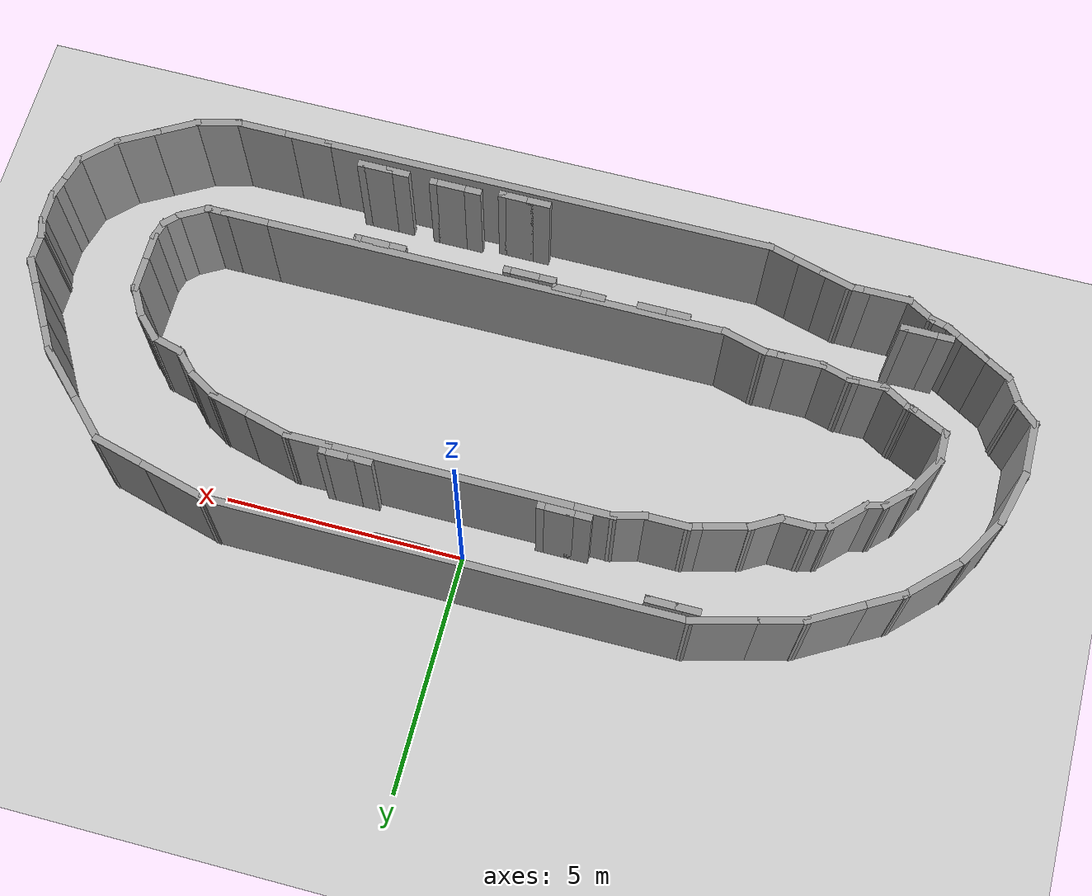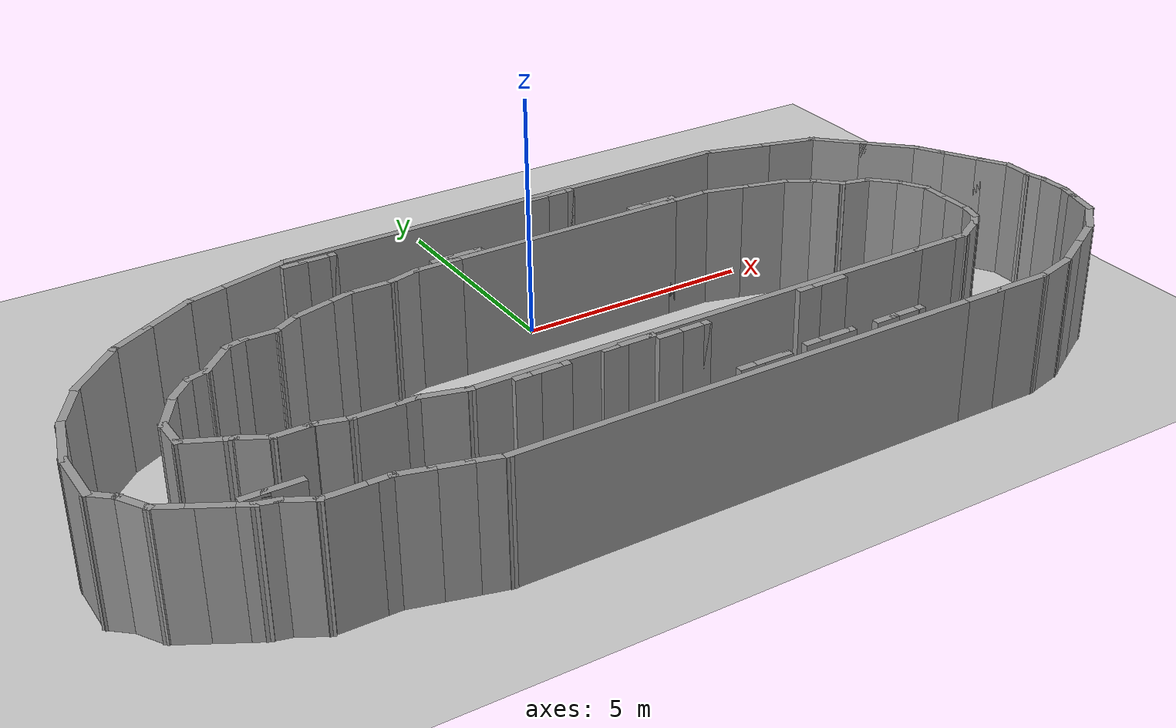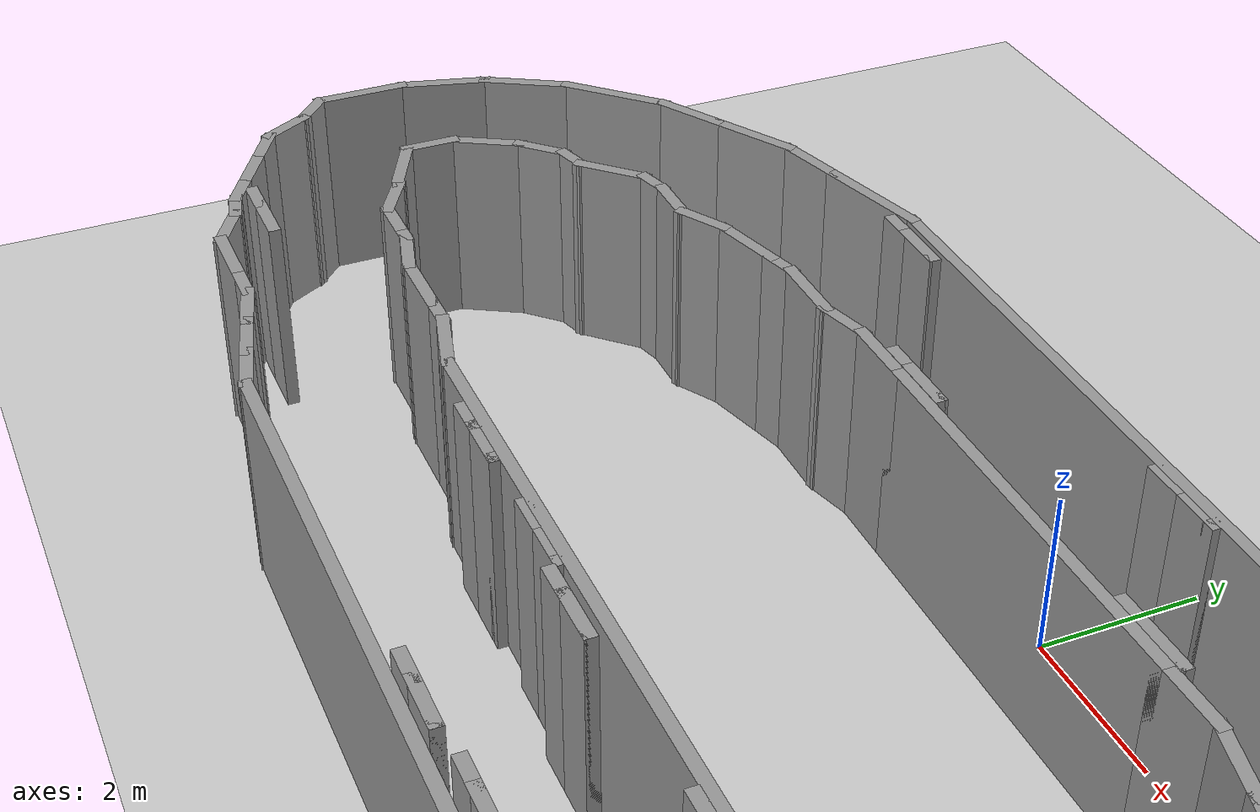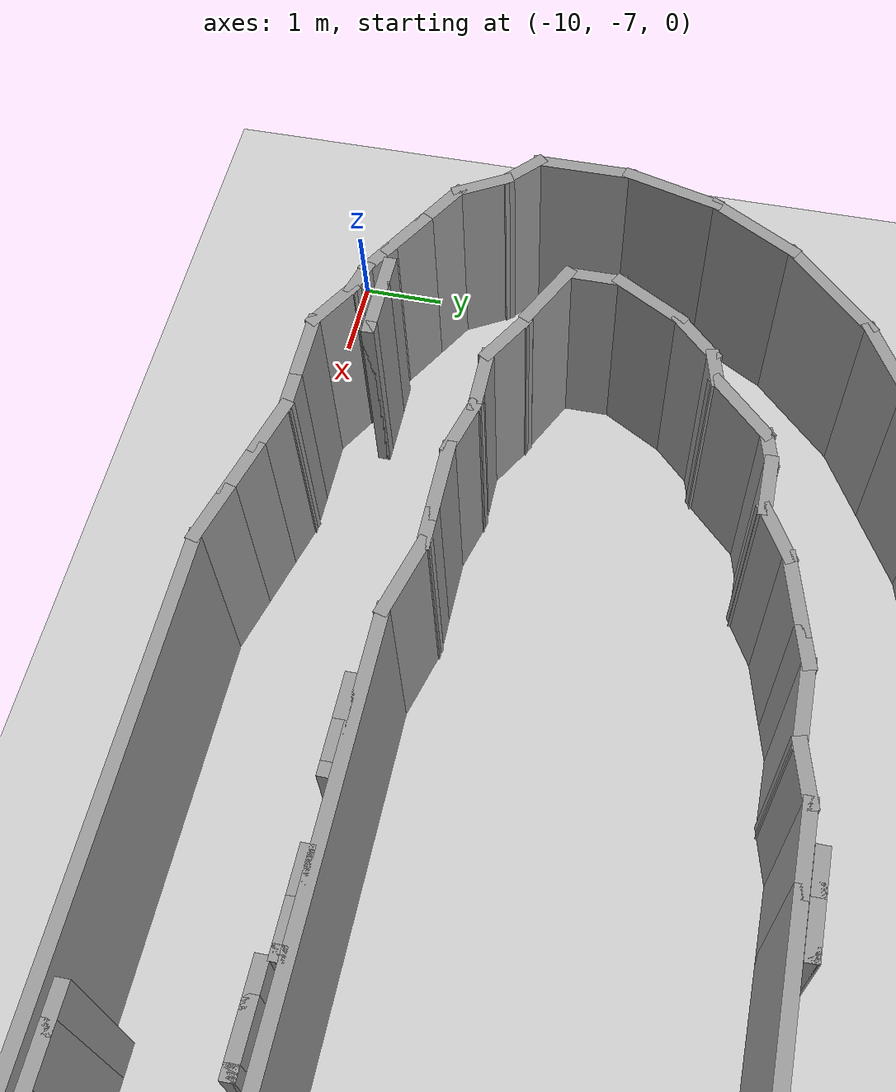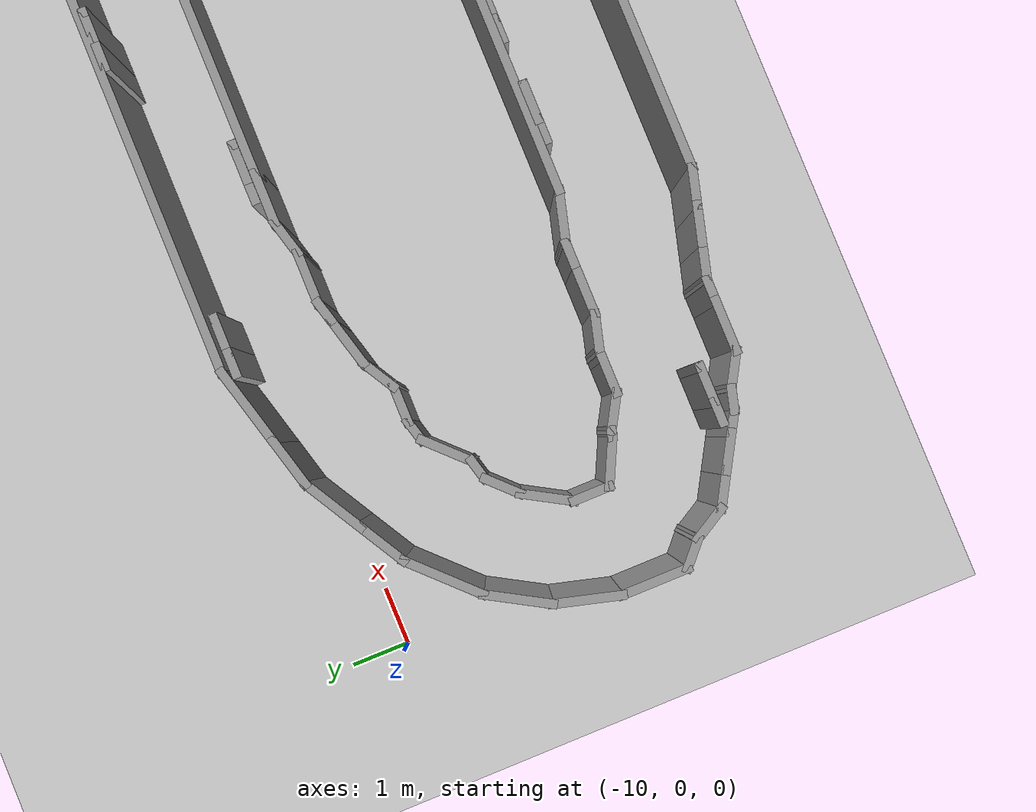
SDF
<sdf version="1.7">
 <world name="default">
  <light name="sun" type="directional">
   <pose>0 0 10 0 -0 0</pose>
   <diffuse>0.8 0.8 0.8 1</diffuse>
   <specular>0.2 0.2 0.2 1</specular>
   <attenuation>
    <range>1000</range>
    <constant>0.9</constant>
    <linear>0.01</linear>
    <quadratic>0.001</quadratic>
   </attenuation>
   <direction>-0.5 0.1 -0.9</direction>
   <spot><inner_angle>0</inner_angle><outer_angle>0</outer_angle><falloff>0</falloff></spot>
  </light>
  <model name="ground_plane">
   <static>1</static>
   <link name="link">
    <collision name="collision">
     <geometry><plane><normal>0 0 1</normal><size>100 100</size></plane></geometry>
     <surface><friction><ode><mu>100</mu><mu2>50</mu2></ode></friction></surface>
    </collision>
    <visual name="visual">
     <cast_shadows>0</cast_shadows>
     <geometry><plane><normal>0 0 1</normal><size>100 100</size></plane></geometry>
     <material>
      <script><uri>file://media/materials/scripts/gazebo.material</uri><name>Gazebo/Grey</name></script>
     </material>
    </visual>
   </link>
  </model>
  <gravity>0 0 -9.8</gravity>
  <magnetic_field>6e-06 2.3e-05 -4.2e-05</magnetic_field>
  <atmosphere type="adiabatic"/>
  <physics type="ode">
   <max_step_size>0.001</max_step_size>
   <real_time_factor>1</real_time_factor>
   <real_time_update_rate>1000</real_time_update_rate>
  </physics>
  <scene><ambient>0.4 0.4 0.4 1</ambient><background>0.7 0.7 0.7 1</background><shadows>1</shadows></scene>
  <spherical_coordinates>
   <surface_model>EARTH_WGS84</surface_model>
   <latitude_deg>0</latitude_deg>
   <longitude_deg>0</longitude_deg>
   <elevation>0</elevation>
   <heading_deg>0</heading_deg>
  </spherical_coordinates>
  <model name="track">
   <pose>-0.221232 -3.17734 0 0 -0 0</pose>
   <link name="Wall_10">
    <collision name="Wall_10_Collision">
     <geometry><box><size>9.75 0.15 2.5</size></box></geometry>
     <pose>0 0 1.25 0 -0 0</pose>
    </collision>
    <visual name="Wall_10_Visual">
     <pose>0 0 1.25 0 -0 0</pose>
     <geometry><box><size>9.75 0.15 2.5</size></box></geometry>
     <material>
      <script><uri>file://media/materials/scripts/gazebo.material</uri><name>Gazebo/Grey</name></script>
      <ambient>1 1 1 1</ambient>
     </material>
     <meta><layer>0</layer></meta>
    </visual>
    <pose>0.289707 4.04592 0 0 -0 0</pose>
   </link>
   <link name="Wall_11">
    <collision name="Wall_11_Collision">
     <geometry><box><size>1.5 0.15 2.5</size></box></geometry>
     <pose>0 0 1.25 0 -0 0</pose>
    </collision>
    <visual name="Wall_11_Visual">
     <pose>0 0 1.25 0 -0 0</pose>
     <geometry><box><size>1.5 0.15 2.5</size></box></geometry>
     <material>
      <script><uri>file://media/materials/scripts/gazebo.material</uri><name>Gazebo/Grey</name></script>
      <ambient>1 1 1 1</ambient>
     </material>
     <meta><layer>0</layer></meta>
    </visual>
    <pose>5.74171 3.87121 0 0 -0 -0.261799</pose>
   </link>
   <link name="Wall_12">
    <collision name="Wall_12_Collision">
     <geometry><box><size>1.25 0.15 2.5</size></box></geometry>
     <pose>0 0 1.25 0 -0 0</pose>
    </collision>
    <visual name="Wall_12_Visual">
     <pose>0 0 1.25 0 -0 0</pose>
     <geometry><box><size>1.25 0.15 2.5</size></box></geometry>
     <material>
      <script><uri>file://media/materials/scripts/gazebo.material</uri><name>Gazebo/Grey</name></script>
      <ambient>1 1 1 1</ambient>
     </material>
     <meta><layer>0</layer></meta>
    </visual>
    <pose>6.92497 3.55416 0 0 -0 -0.261799</pose>
   </link>
   <link name="Wall_13">
    <collision name="Wall_13_Collision">
     <geometry><box><size>1.25 0.15 2.5</size></box></geometry>
     <pose>0 0 1.25 0 -0 0</pose>
    </collision>
    <visual name="Wall_13_Visual">
     <pose>0 0 1.25 0 -0 0</pose>
     <geometry><box><size>1.25 0.15 2.5</size></box></geometry>
     <material>
      <script><uri>file://media/materials/scripts/gazebo.material</uri><name>Gazebo/Grey</name></script>
      <ambient>1 1 1 1</ambient>
     </material>
     <meta><layer>0</layer></meta>
    </visual>
    <pose>7.84513 3.0229 0 0 -0 -0.785398</pose>
   </link>
   <link name="Wall_14">
    <collision name="Wall_14_Collision">
     <geometry><box><size>1.25 0.15 2.5</size></box></geometry>
     <pose>0 0 1.25 0 -0 0</pose>
    </collision>
    <visual name="Wall_14_Visual">
     <pose>0 0 1.25 0 -0 0</pose>
     <geometry><box><size>1.25 0.15 2.5</size></box></geometry>
     <material>
      <script><uri>file://media/materials/scripts/gazebo.material</uri><name>Gazebo/Grey</name></script>
      <ambient>1 1 1 1</ambient>
     </material>
     <meta><layer>0</layer></meta>
    </visual>
    <pose>8.62295 2.24508 0 0 -0 -0.785398</pose>
   </link>
   <link name="Wall_15">
    <collision name="Wall_15_Collision">
     <geometry><box><size>0.75 0.15 2.5</size></box></geometry>
     <pose>0 0 1.25 0 -0 0</pose>
    </collision>
    <visual name="Wall_15_Visual">
     <pose>0 0 1.25 0 -0 0</pose>
     <geometry><box><size>0.75 0.15 2.5</size></box></geometry>
     <material>
      <script><uri>file://media/materials/scripts/gazebo.material</uri><name>Gazebo/Grey</name></script>
      <ambient>1 1 1 1</ambient>
     </material>
     <meta><layer>0</layer></meta>
    </visual>
    <pose>9.16186 1.59637 0 0 -0 -1.0472</pose>
   </link>
   <link name="Wall_16">
    <collision name="Wall_16_Collision">
     <geometry><box><size>1 0.15 2.5</size></box></geometry>
     <pose>0 0 1.25 0 -0 0</pose>
    </collision>
    <visual name="Wall_16_Visual">
     <pose>0 0 1.25 0 -0 0</pose>
     <geometry><box><size>1 0.15 2.5</size></box></geometry>
     <material>
      <script><uri>file://media/materials/scripts/gazebo.material</uri><name>Gazebo/Grey</name></script>
      <ambient>1 1 1 1</ambient>
     </material>
     <meta><layer>0</layer></meta>
    </visual>
    <pose>9.52436 0.9685 0 0 -0 -1.0472</pose>
   </link>
   <link name="Wall_17">
    <collision name="Wall_17_Collision">
     <geometry><box><size>0.75 0.15 2.5</size></box></geometry>
     <pose>0 0 1.25 0 -0 0</pose>
    </collision>
    <visual name="Wall_17_Visual">
     <pose>0 0 1.25 0 -0 0</pose>
     <geometry><box><size>0.75 0.15 2.5</size></box></geometry>
     <material>
      <script><uri>file://media/materials/scripts/gazebo.material</uri><name>Gazebo/Grey</name></script>
      <ambient>1 1 1 1</ambient>
     </material>
     <meta><layer>0</layer></meta>
    </visual>
    <pose>9.88686 0.340631 0 0 -0 -1.0472</pose>
   </link>
   <link name="Wall_18">
    <collision name="Wall_18_Collision">
     <geometry><box><size>0.75 0.15 2.5</size></box></geometry>
     <pose>0 0 1.25 0 -0 0</pose>
    </collision>
    <visual name="Wall_18_Visual">
     <pose>0 0 1.25 0 -0 0</pose>
     <geometry><box><size>0.75 0.15 2.5</size></box></geometry>
     <material>
      <script><uri>file://media/materials/scripts/gazebo.material</uri><name>Gazebo/Grey</name></script>
      <ambient>1 1 1 1</ambient>
     </material>
     <meta><layer>0</layer></meta>
    </visual>
    <pose>10.0369 -0.219177 0 0 -0 -1.5708</pose>
   </link>
   <link name="Wall_19">
    <collision name="Wall_19_Collision">
     <geometry><box><size>0.5 0.15 2.5</size></box></geometry>
     <pose>0 0 1.25 0 -0 0</pose>
    </collision>
    <visual name="Wall_19_Visual">
     <pose>0 0 1.25 0 -0 0</pose>
     <geometry><box><size>0.5 0.15 2.5</size></box></geometry>
     <material>
      <script><uri>file://media/materials/scripts/gazebo.material</uri><name>Gazebo/Grey</name></script>
      <ambient>1 1 1 1</ambient>
     </material>
     <meta><layer>0</layer></meta>
    </visual>
    <pose>10.0822 -0.688213 0 0 -0 -1.309</pose>
   </link>
   <link name="Wall_2">
    <collision name="Wall_2_Collision">
     <geometry><box><size>1.25 0.15 2.5</size></box></geometry>
     <pose>0 0 1.25 0 -0 0</pose>
    </collision>
    <visual name="Wall_2_Visual">
     <pose>0 0 1.25 0 -0 0</pose>
     <geometry><box><size>1.25 0.15 2.5</size></box></geometry>
     <material>
      <script><uri>file://media/materials/scripts/gazebo.material</uri><name>Gazebo/Grey</name></script>
      <ambient>1 1 1 1</ambient>
     </material>
     <meta><layer>0</layer></meta>
    </visual>
    <pose>-10.1134 -1.01822 0 0 -0 1.5708</pose>
   </link>
   <link name="Wall_20">
    <collision name="Wall_20_Collision">
     <geometry><box><size>0.75 0.15 2.5</size></box></geometry>
     <pose>0 0 1.25 0 -0 0</pose>
    </collision>
    <visual name="Wall_20_Visual">
     <pose>0 0 1.25 0 -0 0</pose>
     <geometry><box><size>0.75 0.15 2.5</size></box></geometry>
     <material>
      <script><uri>file://media/materials/scripts/gazebo.material</uri><name>Gazebo/Grey</name></script>
      <ambient>1 1 1 1</ambient>
     </material>
     <meta><layer>0</layer></meta>
    </visual>
    <pose>10.1274 -1.15725 0 0 -0 -1.5708</pose>
   </link>
   <link name="Wall_21">
    <collision name="Wall_21_Collision">
     <geometry><box><size>0.5 0.15 2.5</size></box></geometry>
     <pose>0 0 1.25 0 -0 0</pose>
    </collision>
    <visual name="Wall_21_Visual">
     <pose>0 0 1.25 0 -0 0</pose>
     <geometry><box><size>0.5 0.15 2.5</size></box></geometry>
     <material>
      <script><uri>file://media/materials/scripts/gazebo.material</uri><name>Gazebo/Grey</name></script>
      <ambient>1 1 1 1</ambient>
     </material>
     <meta><layer>0</layer></meta>
    </visual>
    <pose>10.0822 -1.62629 0 0 -0 -1.8326</pose>
   </link>
   <link name="Wall_22">
    <collision name="Wall_22_Collision">
     <geometry><box><size>0.75 0.15 2.5</size></box></geometry>
     <pose>0 0 1.25 0 -0 0</pose>
    </collision>
    <visual name="Wall_22_Visual">
     <pose>0 0 1.25 0 -0 0</pose>
     <geometry><box><size>0.75 0.15 2.5</size></box></geometry>
     <material>
      <script><uri>file://media/materials/scripts/gazebo.material</uri><name>Gazebo/Grey</name></script>
      <ambient>1 1 1 1</ambient>
     </material>
     <meta><layer>0</layer></meta>
    </visual>
    <pose>9.95921 -2.0851 0 0 -0 -1.8326</pose>
   </link>
   <link name="Wall_23">
    <collision name="Wall_23_Collision">
     <geometry><box><size>1 0.15 2.5</size></box></geometry>
     <pose>0 0 1.25 0 -0 0</pose>
    </collision>
    <visual name="Wall_23_Visual">
     <pose>0 0 1.25 0 -0 0</pose>
     <geometry><box><size>1 0.15 2.5</size></box></geometry>
     <material>
      <script><uri>file://media/materials/scripts/gazebo.material</uri><name>Gazebo/Grey</name></script>
      <ambient>1 1 1 1</ambient>
     </material>
     <meta><layer>0</layer></meta>
    </visual>
    <pose>9.58105 -2.6754 0 0 -0 -2.35619</pose>
   </link>
   <link name="Wall_24">
    <collision name="Wall_24_Collision">
     <geometry><box><size>1 0.15 2.5</size></box></geometry>
     <pose>0 0 1.25 0 -0 0</pose>
    </collision>
    <visual name="Wall_24_Visual">
     <pose>0 0 1.25 0 -0 0</pose>
     <geometry><box><size>1 0.15 2.5</size></box></geometry>
     <material>
      <script><uri>file://media/materials/scripts/gazebo.material</uri><name>Gazebo/Grey</name></script>
      <ambient>1 1 1 1</ambient>
     </material>
     <meta><layer>0</layer></meta>
    </visual>
    <pose>8.91247 -3.18842 0 0 -0 -2.61799</pose>
   </link>
   <link name="Wall_25">
    <collision name="Wall_25_Collision">
     <geometry><box><size>1 0.15 2.5</size></box></geometry>
     <pose>0 0 1.25 0 -0 0</pose>
    </collision>
    <visual name="Wall_25_Visual">
     <pose>0 0 1.25 0 -0 0</pose>
     <geometry><box><size>1 0.15 2.5</size></box></geometry>
     <material>
      <script><uri>file://media/materials/scripts/gazebo.material</uri><name>Gazebo/Grey</name></script>
      <ambient>1 1 1 1</ambient>
     </material>
     <meta><layer>0</layer></meta>
    </visual>
    <pose>8.17635 -3.61342 0 0 -0 -2.61799</pose>
   </link>
   <link name="Wall_26">
    <collision name="Wall_26_Collision">
     <geometry><box><size>1 0.15 2.5</size></box></geometry>
     <pose>0 0 1.25 0 -0 0</pose>
    </collision>
    <visual name="Wall_26_Visual">
     <pose>0 0 1.25 0 -0 0</pose>
     <geometry><box><size>1 0.15 2.5</size></box></geometry>
     <material>
      <script><uri>file://media/materials/scripts/gazebo.material</uri><name>Gazebo/Grey</name></script>
      <ambient>1 1 1 1</ambient>
     </material>
     <meta><layer>0</layer></meta>
    </visual>
    <pose>7.39777 -3.93592 0 0 -0 -2.87979</pose>
   </link>
   <link name="Wall_27">
    <collision name="Wall_27_Collision">
     <geometry><box><size>1.25 0.15 2.5</size></box></geometry>
     <pose>0 0 1.25 0 -0 0</pose>
    </collision>
    <visual name="Wall_27_Visual">
     <pose>0 0 1.25 0 -0 0</pose>
     <geometry><box><size>1.25 0.15 2.5</size></box></geometry>
     <material>
      <script><uri>file://media/materials/scripts/gazebo.material</uri><name>Gazebo/Grey</name></script>
      <ambient>1 1 1 1</ambient>
     </material>
     <meta><layer>0</layer></meta>
    </visual>
    <pose>6.43725 -4.04592 0 0 -0 3.14159</pose>
   </link>
   <link name="Wall_28">
    <collision name="Wall_28_Collision">
     <geometry><box><size>1 0.15 2.5</size></box></geometry>
     <pose>0 0 1.25 0 -0 0</pose>
    </collision>
    <visual name="Wall_28_Visual">
     <pose>0 0 1.25 0 -0 0</pose>
     <geometry><box><size>1 0.15 2.5</size></box></geometry>
     <material>
      <script><uri>file://media/materials/scripts/gazebo.material</uri><name>Gazebo/Grey</name></script>
      <ambient>1 1 1 1</ambient>
     </material>
     <meta><layer>0</layer></meta>
    </visual>
    <pose>5.46225 -4.04592 0 0 -0 3.14159</pose>
   </link>
   <link name="Wall_29">
    <collision name="Wall_29_Collision">
     <geometry><box><size>9.5 0.15 2.5</size></box></geometry>
     <pose>0 0 1.25 0 -0 0</pose>
    </collision>
    <visual name="Wall_29_Visual">
     <pose>0 0 1.25 0 -0 0</pose>
     <geometry><box><size>9.5 0.15 2.5</size></box></geometry>
     <material>
      <script><uri>file://media/materials/scripts/gazebo.material</uri><name>Gazebo/Grey</name></script>
      <ambient>1 1 1 1</ambient>
     </material>
     <meta><layer>0</layer></meta>
    </visual>
    <pose>0.362248 -4.04592 0 0 -0 3.14159</pose>
   </link>
   <link name="Wall_3">
    <collision name="Wall_3_Collision">
     <geometry><box><size>1.25 0.15 2.5</size></box></geometry>
     <pose>0 0 1.25 0 -0 0</pose>
    </collision>
    <visual name="Wall_3_Visual">
     <pose>0 0 1.25 0 -0 0</pose>
     <geometry><box><size>1.25 0.15 2.5</size></box></geometry>
     <material>
      <script><uri>file://media/materials/scripts/gazebo.material</uri><name>Gazebo/Grey</name></script>
      <ambient>1 1 1 1</ambient>
     </material>
     <meta><layer>0</layer></meta>
    </visual>
    <pose>-9.97102 0.063034 0 0 -0 1.309</pose>
   </link>
   <link name="Wall_30">
    <collision name="Wall_30_Collision">
     <geometry><box><size>0.75 0.15 2.5</size></box></geometry>
     <pose>0 0 1.25 0 -0 0</pose>
    </collision>
    <visual name="Wall_30_Visual">
     <pose>0 0 1.25 0 -0 0</pose>
     <geometry><box><size>0.75 0.15 2.5</size></box></geometry>
     <material>
      <script><uri>file://media/materials/scripts/gazebo.material</uri><name>Gazebo/Grey</name></script>
      <ambient>1 1 1 1</ambient>
     </material>
     <meta><layer>0</layer></meta>
    </visual>
    <pose>-4.60253 -3.96827 0 0 -0 2.87979</pose>
   </link>
   <link name="Wall_31">
    <collision name="Wall_31_Collision">
     <geometry><box><size>0.75 0.15 2.5</size></box></geometry>
     <pose>0 0 1.25 0 -0 0</pose>
    </collision>
    <visual name="Wall_31_Visual">
     <pose>0 0 1.25 0 -0 0</pose>
     <geometry><box><size>0.75 0.15 2.5</size></box></geometry>
     <material>
      <script><uri>file://media/materials/scripts/gazebo.material</uri><name>Gazebo/Grey</name></script>
      <ambient>1 1 1 1</ambient>
     </material>
     <meta><layer>0</layer></meta>
    </visual>
    <pose>-5.18209 -3.81298 0 0 -0 2.87979</pose>
   </link>
   <link name="Wall_32">
    <collision name="Wall_32_Collision">
     <geometry><box><size>0.75 0.15 2.5</size></box></geometry>
     <pose>0 0 1.25 0 -0 0</pose>
    </collision>
    <visual name="Wall_32_Visual">
     <pose>0 0 1.25 0 -0 0</pose>
     <geometry><box><size>0.75 0.15 2.5</size></box></geometry>
     <material>
      <script><uri>file://media/materials/scripts/gazebo.material</uri><name>Gazebo/Grey</name></script>
      <ambient>1 1 1 1</ambient>
     </material>
     <meta><layer>0</layer></meta>
    </visual>
    <pose>-5.76164 -3.65769 0 0 -0 2.87979</pose>
   </link>
   <link name="Wall_33">
    <collision name="Wall_33_Collision">
     <geometry><box><size>0.5 0.15 2.5</size></box></geometry>
     <pose>0 0 1.25 0 -0 0</pose>
    </collision>
    <visual name="Wall_33_Visual">
     <pose>0 0 1.25 0 -0 0</pose>
     <geometry><box><size>0.5 0.15 2.5</size></box></geometry>
     <material>
      <script><uri>file://media/materials/scripts/gazebo.material</uri><name>Gazebo/Grey</name></script>
      <ambient>1 1 1 1</ambient>
     </material>
     <meta><layer>0</layer></meta>
    </visual>
    <pose>-6.22642 -3.58004 0 0 -0 3.14159</pose>
   </link>
   <link name="Wall_34">
    <collision name="Wall_34_Collision">
     <geometry><box><size>1 0.15 2.5</size></box></geometry>
     <pose>0 0 1.25 0 -0 0</pose>
    </collision>
    <visual name="Wall_34_Visual">
     <pose>0 0 1.25 0 -0 0</pose>
     <geometry><box><size>1 0.15 2.5</size></box></geometry>
     <material>
      <script><uri>file://media/materials/scripts/gazebo.material</uri><name>Gazebo/Grey</name></script>
      <ambient>1 1 1 1</ambient>
     </material>
     <meta><layer>0</layer></meta>
    </visual>
    <pose>-6.82642 -3.58004 0 0 -0 3.14159</pose>
   </link>
   <link name="Wall_35">
    <collision name="Wall_35_Collision">
     <geometry><box><size>0.75 0.15 2.5</size></box></geometry>
     <pose>0 0 1.25 0 -0 0</pose>
    </collision>
    <visual name="Wall_35_Visual">
     <pose>0 0 1.25 0 -0 0</pose>
     <geometry><box><size>0.75 0.15 2.5</size></box></geometry>
     <material>
      <script><uri>file://media/materials/scripts/gazebo.material</uri><name>Gazebo/Grey</name></script>
      <ambient>1 1 1 1</ambient>
     </material>
     <meta><layer>0</layer></meta>
    </visual>
    <pose>-7.51123 -3.43004 0 0 -0 2.61799</pose>
   </link>
   <link name="Wall_36">
    <collision name="Wall_36_Collision">
     <geometry><box><size>0.5 0.15 2.5</size></box></geometry>
     <pose>0 0 1.25 0 -0 0</pose>
    </collision>
    <visual name="Wall_36_Visual">
     <pose>0 0 1.25 0 -0 0</pose>
     <geometry><box><size>0.5 0.15 2.5</size></box></geometry>
     <material>
      <script><uri>file://media/materials/scripts/gazebo.material</uri><name>Gazebo/Grey</name></script>
      <ambient>1 1 1 1</ambient>
     </material>
     <meta><layer>0</layer></meta>
    </visual>
    <pose>-7.94007 -3.23475 0 0 -0 2.87979</pose>
   </link>
   <link name="Wall_37">
    <collision name="Wall_37_Collision">
     <geometry><box><size>0.5 0.15 2.5</size></box></geometry>
     <pose>0 0 1.25 0 -0 0</pose>
    </collision>
    <visual name="Wall_37_Visual">
     <pose>0 0 1.25 0 -0 0</pose>
     <geometry><box><size>0.5 0.15 2.5</size></box></geometry>
     <material>
      <script><uri>file://media/materials/scripts/gazebo.material</uri><name>Gazebo/Grey</name></script>
      <ambient>1 1 1 1</ambient>
     </material>
     <meta><layer>0</layer></meta>
    </visual>
    <pose>-8.26066 -3.10196 0 0 -0 2.61799</pose>
   </link>
   <link name="Wall_38">
    <collision name="Wall_38_Collision">
     <geometry><box><size>0.75 0.15 2.5</size></box></geometry>
     <pose>0 0 1.25 0 -0 0</pose>
    </collision>
    <visual name="Wall_38_Visual">
     <pose>0 0 1.25 0 -0 0</pose>
     <geometry><box><size>0.75 0.15 2.5</size></box></geometry>
     <material>
      <script><uri>file://media/materials/scripts/gazebo.material</uri><name>Gazebo/Grey</name></script>
      <ambient>1 1 1 1</ambient>
     </material>
     <meta><layer>0</layer></meta>
    </visual>
    <pose>-8.67202 -2.86446 0 0 -0 2.61799</pose>
   </link>
   <link name="Wall_39">
    <collision name="Wall_39_Collision">
     <geometry><box><size>0.75 0.15 2.5</size></box></geometry>
     <pose>0 0 1.25 0 -0 0</pose>
    </collision>
    <visual name="Wall_39_Visual">
     <pose>0 0 1.25 0 -0 0</pose>
     <geometry><box><size>0.75 0.15 2.5</size></box></geometry>
     <material>
      <script><uri>file://media/materials/scripts/gazebo.material</uri><name>Gazebo/Grey</name></script>
      <ambient>1 1 1 1</ambient>
     </material>
     <meta><layer>0</layer></meta>
    </visual>
    <pose>-9.19164 -2.56446 0 0 -0 2.61799</pose>
   </link>
   <link name="Wall_4">
    <collision name="Wall_4_Collision">
     <geometry><box><size>1.25 0.15 2.5</size></box></geometry>
     <pose>0 0 1.25 0 -0 0</pose>
    </collision>
    <visual name="Wall_4_Visual">
     <pose>0 0 1.25 0 -0 0</pose>
     <geometry><box><size>1.25 0.15 2.5</size></box></geometry>
     <material>
      <script><uri>file://media/materials/scripts/gazebo.material</uri><name>Gazebo/Grey</name></script>
      <ambient>1 1 1 1</ambient>
     </material>
     <meta><layer>0</layer></meta>
    </visual>
    <pose>-9.55367 1.07061 0 0 -0 1.0472</pose>
   </link>
   <link name="Wall_40">
    <collision name="Wall_40_Collision">
     <geometry><box><size>0.75 0.15 2.5</size></box></geometry>
     <pose>0 0 1.25 0 -0 0</pose>
    </collision>
    <visual name="Wall_40_Visual">
     <pose>0 0 1.25 0 -0 0</pose>
     <geometry><box><size>0.75 0.15 2.5</size></box></geometry>
     <material>
      <script><uri>file://media/materials/scripts/gazebo.material</uri><name>Gazebo/Grey</name></script>
      <ambient>1 1 1 1</ambient>
     </material>
     <meta><layer>0</layer></meta>
    </visual>
    <pose>-9.60145 -2.15465 0 0 -0 2.0944</pose>
   </link>
   <link name="Wall_41">
    <collision name="Wall_41_Collision">
     <geometry><box><size>0.637513 0.15 2.5</size></box></geometry>
     <pose>0 0 1.25 0 -0 0</pose>
    </collision>
    <visual name="Wall_41_Visual">
     <pose>0 0 1.25 0 -0 0</pose>
     <geometry><box><size>0.637513 0.15 2.5</size></box></geometry>
     <material>
      <script><uri>file://media/materials/scripts/gazebo.material</uri><name>Gazebo/Grey</name></script>
      <ambient>1 1 1 1</ambient>
     </material>
     <meta><layer>0</layer></meta>
    </visual>
    <pose>-9.93241 -1.73153 0 0 -0 2.40743</pose>
   </link>
   <link name="Wall_44">
    <collision name="Wall_44_Collision">
     <geometry><box><size>0.75 0.15 2.5</size></box></geometry>
     <pose>0 0 1.25 0 -0 0</pose>
    </collision>
    <visual name="Wall_44_Visual">
     <pose>0 0 1.25 0 -0 0</pose>
     <geometry><box><size>0.75 0.15 2.5</size></box></geometry>
     <material>
      <script><uri>file://media/materials/scripts/gazebo.material</uri><name>Gazebo/Grey</name></script>
      <ambient>1 1 1 1</ambient>
     </material>
     <meta><layer>0</layer></meta>
    </visual>
    <pose>-8.46711 -0.620568 0 0 -0 1.5708</pose>
   </link>
   <link name="Wall_45">
    <collision name="Wall_45_Collision">
     <geometry><box><size>1 0.15 2.5</size></box></geometry>
     <pose>0 0 1.25 0 -0 0</pose>
    </collision>
    <visual name="Wall_45_Visual">
     <pose>0 0 1.25 0 -0 0</pose>
     <geometry><box><size>1 0.15 2.5</size></box></geometry>
     <material>
      <script><uri>file://media/materials/scripts/gazebo.material</uri><name>Gazebo/Grey</name></script>
      <ambient>1 1 1 1</ambient>
     </material>
     <meta><layer>0</layer></meta>
    </visual>
    <pose>-8.25461 0.047493 0 0 -0 1.0472</pose>
   </link>
   <link name="Wall_46">
    <collision name="Wall_46_Collision">
     <geometry><box><size>0.75 0.15 2.5</size></box></geometry>
     <pose>0 0 1.25 0 -0 0</pose>
    </collision>
    <visual name="Wall_46_Visual">
     <pose>0 0 1.25 0 -0 0</pose>
     <geometry><box><size>0.75 0.15 2.5</size></box></geometry>
     <material>
      <script><uri>file://media/materials/scripts/gazebo.material</uri><name>Gazebo/Grey</name></script>
      <ambient>1 1 1 1</ambient>
     </material>
     <meta><layer>0</layer></meta>
    </visual>
    <pose>-7.82998 0.627685 0 0 -0 0.785398</pose>
   </link>
   <link name="Wall_47">
    <collision name="Wall_47_Collision">
     <geometry><box><size>0.5 0.15 2.5</size></box></geometry>
     <pose>0 0 1.25 0 -0 0</pose>
    </collision>
    <visual name="Wall_47_Visual">
     <pose>0 0 1.25 0 -0 0</pose>
     <geometry><box><size>0.5 0.15 2.5</size></box></geometry>
     <material>
      <script><uri>file://media/materials/scripts/gazebo.material</uri><name>Gazebo/Grey</name></script>
      <ambient>1 1 1 1</ambient>
     </material>
     <meta><layer>0</layer></meta>
    </visual>
    <pose>-7.44881 0.885111 0 0 -0 0.261799</pose>
   </link>
   <link name="Wall_48">
    <collision name="Wall_48_Collision">
     <geometry><box><size>1 0.15 2.5</size></box></geometry>
     <pose>0 0 1.25 0 -0 0</pose>
    </collision>
    <visual name="Wall_48_Visual">
     <pose>0 0 1.25 0 -0 0</pose>
     <geometry><box><size>1 0.15 2.5</size></box></geometry>
     <material>
      <script><uri>file://media/materials/scripts/gazebo.material</uri><name>Gazebo/Grey</name></script>
      <ambient>1 1 1 1</ambient>
     </material>
     <meta><layer>0</layer></meta>
    </visual>
    <pose>-6.97926 1.23092 0 0 -0 0.785398</pose>
   </link>
   <link name="Wall_49">
    <collision name="Wall_49_Collision">
     <geometry><box><size>0.5 0.15 2.5</size></box></geometry>
     <pose>0 0 1.25 0 -0 0</pose>
    </collision>
    <visual name="Wall_49_Visual">
     <pose>0 0 1.25 0 -0 0</pose>
     <geometry><box><size>0.5 0.15 2.5</size></box></geometry>
     <material>
      <script><uri>file://media/materials/scripts/gazebo.material</uri><name>Gazebo/Grey</name></script>
      <ambient>1 1 1 1</ambient>
     </material>
     <meta><layer>0</layer></meta>
    </visual>
    <pose>-6.5097 1.57674 0 0 -0 0.261799</pose>
   </link>
   <link name="Wall_5">
    <collision name="Wall_5_Collision">
     <geometry><box><size>1.5 0.15 2.5</size></box></geometry>
     <pose>0 0 1.25 0 -0 0</pose>
    </collision>
    <visual name="Wall_5_Visual">
     <pose>0 0 1.25 0 -0 0</pose>
     <geometry><box><size>1.5 0.15 2.5</size></box></geometry>
     <material>
      <script><uri>file://media/materials/scripts/gazebo.material</uri><name>Gazebo/Grey</name></script>
      <ambient>1 1 1 1</ambient>
     </material>
     <meta><layer>0</layer></meta>
    </visual>
    <pose>-8.80138 2.02422 0 0 -0 0.785398</pose>
   </link>
   <link name="Wall_50">
    <collision name="Wall_50_Collision">
     <geometry><box><size>0.75 0.15 2.5</size></box></geometry>
     <pose>0 0 1.25 0 -0 0</pose>
    </collision>
    <visual name="Wall_50_Visual">
     <pose>0 0 1.25 0 -0 0</pose>
     <geometry><box><size>0.75 0.15 2.5</size></box></geometry>
     <material>
      <script><uri>file://media/materials/scripts/gazebo.material</uri><name>Gazebo/Grey</name></script>
      <ambient>1 1 1 1</ambient>
     </material>
     <meta><layer>0</layer></meta>
    </visual>
    <pose>-6.04066 1.62203 0 0 -0 0</pose>
   </link>
   <link name="Wall_51">
    <collision name="Wall_51_Collision">
     <geometry><box><size>0.75 0.15 2.5</size></box></geometry>
     <pose>0 0 1.25 0 -0 0</pose>
    </collision>
    <visual name="Wall_51_Visual">
     <pose>0 0 1.25 0 -0 0</pose>
     <geometry><box><size>0.75 0.15 2.5</size></box></geometry>
     <material>
      <script><uri>file://media/materials/scripts/gazebo.material</uri><name>Gazebo/Grey</name></script>
      <ambient>1 1 1 1</ambient>
     </material>
     <meta><layer>0</layer></meta>
    </visual>
    <pose>-5.48085 1.77203 0 0 -0 0.523599</pose>
   </link>
   <link name="Wall_52">
    <collision name="Wall_52_Collision">
     <geometry><box><size>1 0.15 2.5</size></box></geometry>
     <pose>0 0 1.25 0 -0 0</pose>
    </collision>
    <visual name="Wall_52_Visual">
     <pose>0 0 1.25 0 -0 0</pose>
     <geometry><box><size>1 0.15 2.5</size></box></geometry>
     <material>
      <script><uri>file://media/materials/scripts/gazebo.material</uri><name>Gazebo/Grey</name></script>
      <ambient>1 1 1 1</ambient>
     </material>
     <meta><layer>0</layer></meta>
    </visual>
    <pose>-4.81053 2.03203 0 0 -0 0.261799</pose>
   </link>
   <link name="Wall_53">
    <collision name="Wall_53_Collision">
     <geometry><box><size>0.5 0.15 2.5</size></box></geometry>
     <pose>0 0 1.25 0 -0 0</pose>
    </collision>
    <visual name="Wall_53_Visual">
     <pose>0 0 1.25 0 -0 0</pose>
     <geometry><box><size>0.5 0.15 2.5</size></box></geometry>
     <material>
      <script><uri>file://media/materials/scripts/gazebo.material</uri><name>Gazebo/Grey</name></script>
      <ambient>1 1 1 1</ambient>
     </material>
     <meta><layer>0</layer></meta>
    </visual>
    <pose>-4.23097 2.18732 0 0 -0 0.261799</pose>
   </link>
   <link name="Wall_54">
    <collision name="Wall_54_Collision">
     <geometry><box><size>1 0.15 2.5</size></box></geometry>
     <pose>0 0 1.25 0 -0 0</pose>
    </collision>
    <visual name="Wall_54_Visual">
     <pose>0 0 1.25 0 -0 0</pose>
     <geometry><box><size>1 0.15 2.5</size></box></geometry>
     <material>
      <script><uri>file://media/materials/scripts/gazebo.material</uri><name>Gazebo/Grey</name></script>
      <ambient>1 1 1 1</ambient>
     </material>
     <meta><layer>0</layer></meta>
    </visual>
    <pose>-3.63693 2.23261 0 0 -0 0</pose>
   </link>
   <link name="Wall_55">
    <collision name="Wall_55_Collision">
     <geometry><box><size>0.75 0.15 2.5</size></box></geometry>
     <pose>0 0 1.25 0 -0 0</pose>
    </collision>
    <visual name="Wall_55_Visual">
     <pose>0 0 1.25 0 -0 0</pose>
     <geometry><box><size>0.75 0.15 2.5</size></box></geometry>
     <material>
      <script><uri>file://media/materials/scripts/gazebo.material</uri><name>Gazebo/Grey</name></script>
      <ambient>1 1 1 1</ambient>
     </material>
     <meta><layer>0</layer></meta>
    </visual>
    <pose>-2.92216 2.31026 0 0 -0 0.261799</pose>
   </link>
   <link name="Wall_56">
    <collision name="Wall_56_Collision">
     <geometry><box><size>1 0.15 2.5</size></box></geometry>
     <pose>0 0 1.25 0 -0 0</pose>
    </collision>
    <visual name="Wall_56_Visual">
     <pose>0 0 1.25 0 -0 0</pose>
     <geometry><box><size>1 0.15 2.5</size></box></geometry>
     <material>
      <script><uri>file://media/materials/scripts/gazebo.material</uri><name>Gazebo/Grey</name></script>
      <ambient>1 1 1 1</ambient>
     </material>
     <meta><layer>0</layer></meta>
    </visual>
    <pose>-2.20738 2.38791 0 0 -0 0</pose>
   </link>
   <link name="Wall_57">
    <collision name="Wall_57_Collision">
     <geometry><box><size>5 0.15 2.5</size></box></geometry>
     <pose>0 0 1.25 0 -0 0</pose>
    </collision>
    <visual name="Wall_57_Visual">
     <pose>0 0 1.25 0 -0 0</pose>
     <geometry><box><size>5 0.15 2.5</size></box></geometry>
     <material>
      <script><uri>file://media/materials/scripts/gazebo.material</uri><name>Gazebo/Grey</name></script>
      <ambient>1 1 1 1</ambient>
     </material>
     <meta><layer>0</layer></meta>
    </visual>
    <pose>0.642621 2.38791 0 0 -0 0</pose>
   </link>
   <link name="Wall_58">
    <collision name="Wall_58_Collision">
     <geometry><box><size>1 0.15 2.5</size></box></geometry>
     <pose>0 0 1.25 0 -0 0</pose>
    </collision>
    <visual name="Wall_58_Visual">
     <pose>0 0 1.25 0 -0 0</pose>
     <geometry><box><size>1 0.15 2.5</size></box></geometry>
     <material>
      <script><uri>file://media/materials/scripts/gazebo.material</uri><name>Gazebo/Grey</name></script>
      <ambient>1 1 1 1</ambient>
     </material>
     <meta><layer>0</layer></meta>
    </visual>
    <pose>3.49262 2.38791 0 0 -0 0</pose>
   </link>
   <link name="Wall_59">
    <collision name="Wall_59_Collision">
     <geometry><box><size>1 0.15 2.5</size></box></geometry>
     <pose>0 0 1.25 0 -0 0</pose>
    </collision>
    <visual name="Wall_59_Visual">
     <pose>0 0 1.25 0 -0 0</pose>
     <geometry><box><size>1 0.15 2.5</size></box></geometry>
     <material>
      <script><uri>file://media/materials/scripts/gazebo.material</uri><name>Gazebo/Grey</name></script>
      <ambient>1 1 1 1</ambient>
     </material>
     <meta><layer>0</layer></meta>
    </visual>
    <pose>4.32814 2.27791 0 0 -0 -0.261799</pose>
   </link>
   <link name="Wall_6">
    <collision name="Wall_6_Collision">
     <geometry><box><size>1 0.15 2.5</size></box></geometry>
     <pose>0 0 1.25 0 -0 0</pose>
    </collision>
    <visual name="Wall_6_Visual">
     <pose>0 0 1.25 0 -0 0</pose>
     <geometry><box><size>1 0.15 2.5</size></box></geometry>
     <material>
      <script><uri>file://media/materials/scripts/gazebo.material</uri><name>Gazebo/Grey</name></script>
      <ambient>1 1 1 1</ambient>
     </material>
     <meta><layer>0</layer></meta>
    </visual>
    <pose>-7.95602 2.71401 0 0 -0 0.523599</pose>
   </link>
   <link name="Wall_60">
    <collision name="Wall_60_Collision">
     <geometry><box><size>1 0.15 2.5</size></box></geometry>
     <pose>0 0 1.25 0 -0 0</pose>
    </collision>
    <visual name="Wall_60_Visual">
     <pose>0 0 1.25 0 -0 0</pose>
     <geometry><box><size>1 0.15 2.5</size></box></geometry>
     <material>
      <script><uri>file://media/materials/scripts/gazebo.material</uri><name>Gazebo/Grey</name></script>
      <ambient>1 1 1 1</ambient>
     </material>
     <meta><layer>0</layer></meta>
    </visual>
    <pose>5.14918 2.05791 0 0 -0 -0.261799</pose>
   </link>
   <link name="Wall_61">
    <collision name="Wall_61_Collision">
     <geometry><box><size>0.75 0.15 2.5</size></box></geometry>
     <pose>0 0 1.25 0 -0 0</pose>
    </collision>
    <visual name="Wall_61_Visual">
     <pose>0 0 1.25 0 -0 0</pose>
     <geometry><box><size>0.75 0.15 2.5</size></box></geometry>
     <material>
      <script><uri>file://media/materials/scripts/gazebo.material</uri><name>Gazebo/Grey</name></script>
      <ambient>1 1 1 1</ambient>
     </material>
     <meta><layer>0</layer></meta>
    </visual>
    <pose>5.8195 1.79791 0 0 -0 -0.523599</pose>
   </link>
   <link name="Wall_62">
    <collision name="Wall_62_Collision">
     <geometry><box><size>0.75 0.15 2.5</size></box></geometry>
     <pose>0 0 1.25 0 -0 0</pose>
    </collision>
    <visual name="Wall_62_Visual">
     <pose>0 0 1.25 0 -0 0</pose>
     <geometry><box><size>0.75 0.15 2.5</size></box></geometry>
     <material>
      <script><uri>file://media/materials/scripts/gazebo.material</uri><name>Gazebo/Grey</name></script>
      <ambient>1 1 1 1</ambient>
     </material>
     <meta><layer>0</layer></meta>
    </visual>
    <pose>6.29144 1.43578 0 0 -0 -0.785398</pose>
   </link>
   <link name="Wall_63">
    <collision name="Wall_63_Collision">
     <geometry><box><size>0.75 0.15 2.5</size></box></geometry>
     <pose>0 0 1.25 0 -0 0</pose>
    </collision>
    <visual name="Wall_63_Visual">
     <pose>0 0 1.25 0 -0 0</pose>
     <geometry><box><size>0.75 0.15 2.5</size></box></geometry>
     <material>
      <script><uri>file://media/materials/scripts/gazebo.material</uri><name>Gazebo/Grey</name></script>
      <ambient>1 1 1 1</ambient>
     </material>
     <meta><layer>0</layer></meta>
    </visual>
    <pose>6.79335 1.146 0 0 -0 -0.261799</pose>
   </link>
   <link name="Wall_64">
    <collision name="Wall_64_Collision">
     <geometry><box><size>0.75 0.15 2.5</size></box></geometry>
     <pose>0 0 1.25 0 -0 0</pose>
    </collision>
    <visual name="Wall_64_Visual">
     <pose>0 0 1.25 0 -0 0</pose>
     <geometry><box><size>0.75 0.15 2.5</size></box></geometry>
     <material>
      <script><uri>file://media/materials/scripts/gazebo.material</uri><name>Gazebo/Grey</name></script>
      <ambient>1 1 1 1</ambient>
     </material>
     <meta><layer>0</layer></meta>
    </visual>
    <pose>7.29526 0.856226 0 0 -0 -0.785398</pose>
   </link>
   <link name="Wall_65">
    <collision name="Wall_65_Collision">
     <geometry><box><size>0.75 0.15 2.5</size></box></geometry>
     <pose>0 0 1.25 0 -0 0</pose>
    </collision>
    <visual name="Wall_65_Visual">
     <pose>0 0 1.25 0 -0 0</pose>
     <geometry><box><size>0.75 0.15 2.5</size></box></geometry>
     <material>
      <script><uri>file://media/materials/scripts/gazebo.material</uri><name>Gazebo/Grey</name></script>
      <ambient>1 1 1 1</ambient>
     </material>
     <meta><layer>0</layer></meta>
    </visual>
    <pose>7.65739 0.384286 0 0 -0 -1.0472</pose>
   </link>
   <link name="Wall_66">
    <collision name="Wall_66_Collision">
     <geometry><box><size>0.75 0.15 2.5</size></box></geometry>
     <pose>0 0 1.25 0 -0 0</pose>
    </collision>
    <visual name="Wall_66_Visual">
     <pose>0 0 1.25 0 -0 0</pose>
     <geometry><box><size>0.75 0.15 2.5</size></box></geometry>
     <material>
      <script><uri>file://media/materials/scripts/gazebo.material</uri><name>Gazebo/Grey</name></script>
      <ambient>1 1 1 1</ambient>
     </material>
     <meta><layer>0</layer></meta>
    </visual>
    <pose>7.80739 -0.175521 0 0 -0 -1.5708</pose>
   </link>
   <link name="Wall_67">
    <collision name="Wall_67_Collision">
     <geometry><box><size>0.75 0.15 2.5</size></box></geometry>
     <pose>0 0 1.25 0 -0 0</pose>
    </collision>
    <visual name="Wall_67_Visual">
     <pose>0 0 1.25 0 -0 0</pose>
     <geometry><box><size>0.75 0.15 2.5</size></box></geometry>
     <material>
      <script><uri>file://media/materials/scripts/gazebo.material</uri><name>Gazebo/Grey</name></script>
      <ambient>1 1 1 1</ambient>
     </material>
     <meta><layer>0</layer></meta>
    </visual>
    <pose>7.80739 -0.775521 0 0 -0 -1.5708</pose>
   </link>
   <link name="Wall_68">
    <collision name="Wall_68_Collision">
     <geometry><box><size>0.5 0.15 2.5</size></box></geometry>
     <pose>0 0 1.25 0 -0 0</pose>
    </collision>
    <visual name="Wall_68_Visual">
     <pose>0 0 1.25 0 -0 0</pose>
     <geometry><box><size>0.5 0.15 2.5</size></box></geometry>
     <material>
      <script><uri>file://media/materials/scripts/gazebo.material</uri><name>Gazebo/Grey</name></script>
      <ambient>1 1 1 1</ambient>
     </material>
     <meta><layer>0</layer></meta>
    </visual>
    <pose>7.7621 -1.24456 0 0 -0 -1.8326</pose>
   </link>
   <link name="Wall_69">
    <collision name="Wall_69_Collision">
     <geometry><box><size>0.5 0.15 2.5</size></box></geometry>
     <pose>0 0 1.25 0 -0 0</pose>
    </collision>
    <visual name="Wall_69_Visual">
     <pose>0 0 1.25 0 -0 0</pose>
     <geometry><box><size>0.5 0.15 2.5</size></box></geometry>
     <material>
      <script><uri>file://media/materials/scripts/gazebo.material</uri><name>Gazebo/Grey</name></script>
      <ambient>1 1 1 1</ambient>
     </material>
     <meta><layer>0</layer></meta>
    </visual>
    <pose>7.59306 -1.53734 0 0 -0 -2.35619</pose>
   </link>
   <link name="Wall_7">
    <collision name="Wall_7_Collision">
     <geometry><box><size>1.25 0.15 2.5</size></box></geometry>
     <pose>0 0 1.25 0 -0 0</pose>
    </collision>
    <visual name="Wall_7_Visual">
     <pose>0 0 1.25 0 -0 0</pose>
     <geometry><box><size>1.25 0.15 2.5</size></box></geometry>
     <material>
      <script><uri>file://media/materials/scripts/gazebo.material</uri><name>Gazebo/Grey</name></script>
      <ambient>1 1 1 1</ambient>
     </material>
     <meta><layer>0</layer></meta>
    </visual>
    <pose>-7.11164 3.20152 0 0 -0 0.523599</pose>
   </link>
   <link name="Wall_70">
    <collision name="Wall_70_Collision">
     <geometry><box><size>0.75 0.15 2.5</size></box></geometry>
     <pose>0 0 1.25 0 -0 0</pose>
    </collision>
    <visual name="Wall_70_Visual">
     <pose>0 0 1.25 0 -0 0</pose>
     <geometry><box><size>0.75 0.15 2.5</size></box></geometry>
     <material>
      <script><uri>file://media/materials/scripts/gazebo.material</uri><name>Gazebo/Grey</name></script>
      <ambient>1 1 1 1</ambient>
     </material>
     <meta><layer>0</layer></meta>
    </visual>
    <pose>7.20951 -1.81108 0 0 -0 -2.61799</pose>
   </link>
   <link name="Wall_71">
    <collision name="Wall_71_Collision">
     <geometry><box><size>0.5 0.15 2.5</size></box></geometry>
     <pose>0 0 1.25 0 -0 0</pose>
    </collision>
    <visual name="Wall_71_Visual">
     <pose>0 0 1.25 0 -0 0</pose>
     <geometry><box><size>0.5 0.15 2.5</size></box></geometry>
     <material>
      <script><uri>file://media/materials/scripts/gazebo.material</uri><name>Gazebo/Grey</name></script>
      <ambient>1 1 1 1</ambient>
     </material>
     <meta><layer>0</layer></meta>
    </visual>
    <pose>6.7747 -1.96108 0 0 -0 3.14159</pose>
   </link>
   <link name="Wall_72">
    <collision name="Wall_72_Collision">
     <geometry><box><size>1 0.15 2.5</size></box></geometry>
     <pose>0 0 1.25 0 -0 0</pose>
    </collision>
    <visual name="Wall_72_Visual">
     <pose>0 0 1.25 0 -0 0</pose>
     <geometry><box><size>1 0.15 2.5</size></box></geometry>
     <material>
      <script><uri>file://media/materials/scripts/gazebo.material</uri><name>Gazebo/Grey</name></script>
      <ambient>1 1 1 1</ambient>
     </material>
     <meta><layer>0</layer></meta>
    </visual>
    <pose>6.17471 -1.96108 0 0 -0 3.14159</pose>
   </link>
   <link name="Wall_73">
    <collision name="Wall_73_Collision">
     <geometry><box><size>9.75 0.15 2.5</size></box></geometry>
     <pose>0 0 1.25 0 -0 0</pose>
    </collision>
    <visual name="Wall_73_Visual">
     <pose>0 0 1.25 0 -0 0</pose>
     <geometry><box><size>9.75 0.15 2.5</size></box></geometry>
     <material>
      <script><uri>file://media/materials/scripts/gazebo.material</uri><name>Gazebo/Grey</name></script>
      <ambient>1 1 1 1</ambient>
     </material>
     <meta><layer>0</layer></meta>
    </visual>
    <pose>0.949705 -1.96108 0 0 -0 3.14159</pose>
   </link>
   <link name="Wall_74">
    <collision name="Wall_74_Collision">
     <geometry><box><size>1 0.15 2.5</size></box></geometry>
     <pose>0 0 1.25 0 -0 0</pose>
    </collision>
    <visual name="Wall_74_Visual">
     <pose>0 0 1.25 0 -0 0</pose>
     <geometry><box><size>1 0.15 2.5</size></box></geometry>
     <material>
      <script><uri>file://media/materials/scripts/gazebo.material</uri><name>Gazebo/Grey</name></script>
      <ambient>1 1 1 1</ambient>
     </material>
     <meta><layer>0</layer></meta>
    </visual>
    <pose>-4.26081 -1.85109 0 0 -0 2.87979</pose>
   </link>
   <link name="Wall_75">
    <collision name="Wall_75_Collision">
     <geometry><box><size>0.5 0.15 2.5</size></box></geometry>
     <pose>0 0 1.25 0 -0 0</pose>
    </collision>
    <visual name="Wall_75_Visual">
     <pose>0 0 1.25 0 -0 0</pose>
     <geometry><box><size>0.5 0.15 2.5</size></box></geometry>
     <material>
      <script><uri>file://media/materials/scripts/gazebo.material</uri><name>Gazebo/Grey</name></script>
      <ambient>1 1 1 1</ambient>
     </material>
     <meta><layer>0</layer></meta>
    </visual>
    <pose>-4.84633 -1.74109 0 0 -0 3.14159</pose>
   </link>
   <link name="Wall_76">
    <collision name="Wall_76_Collision">
     <geometry><box><size>1 0.15 2.5</size></box></geometry>
     <pose>0 0 1.25 0 -0 0</pose>
    </collision>
    <visual name="Wall_76_Visual">
     <pose>0 0 1.25 0 -0 0</pose>
     <geometry><box><size>1 0.15 2.5</size></box></geometry>
     <material>
      <script><uri>file://media/materials/scripts/gazebo.material</uri><name>Gazebo/Grey</name></script>
      <ambient>1 1 1 1</ambient>
     </material>
     <meta><layer>0</layer></meta>
    </visual>
    <pose>-5.44633 -1.74109 0 0 -0 3.14159</pose>
   </link>
   <link name="Wall_77">
    <collision name="Wall_77_Collision">
     <geometry><box><size>0.75 0.15 2.5</size></box></geometry>
     <pose>0 0 1.25 0 -0 0</pose>
    </collision>
    <visual name="Wall_77_Visual">
     <pose>0 0 1.25 0 -0 0</pose>
     <geometry><box><size>0.75 0.15 2.5</size></box></geometry>
     <material>
      <script><uri>file://media/materials/scripts/gazebo.material</uri><name>Gazebo/Grey</name></script>
      <ambient>1 1 1 1</ambient>
     </material>
     <meta><layer>0</layer></meta>
    </visual>
    <pose>-6.16111 -1.66344 0 0 -0 2.87979</pose>
   </link>
   <link name="Wall_78">
    <collision name="Wall_78_Collision">
     <geometry><box><size>0.25 0.15 2.5</size></box></geometry>
     <pose>0 0 1.25 0 -0 0</pose>
    </collision>
    <visual name="Wall_78_Visual">
     <pose>0 0 1.25 0 -0 0</pose>
     <geometry><box><size>0.25 0.15 2.5</size></box></geometry>
     <material>
      <script><uri>file://media/materials/scripts/gazebo.material</uri><name>Gazebo/Grey</name></script>
      <ambient>1 1 1 1</ambient>
     </material>
     <meta><layer>0</layer></meta>
    </visual>
    <pose>-6.50089 -1.5858 0 0 -0 3.14159</pose>
   </link>
   <link name="Wall_79">
    <collision name="Wall_79_Collision">
     <geometry><box><size>0.75 0.15 2.5</size></box></geometry>
     <pose>0 0 1.25 0 -0 0</pose>
    </collision>
    <visual name="Wall_79_Visual">
     <pose>0 0 1.25 0 -0 0</pose>
     <geometry><box><size>0.75 0.15 2.5</size></box></geometry>
     <material>
      <script><uri>file://media/materials/scripts/gazebo.material</uri><name>Gazebo/Grey</name></script>
      <ambient>1 1 1 1</ambient>
     </material>
     <meta><layer>0</layer></meta>
    </visual>
    <pose>-6.85089 -1.5858 0 0 -0 3.14159</pose>
   </link>
   <link name="Wall_8">
    <collision name="Wall_8_Collision">
     <geometry><box><size>1 0.15 2.5</size></box></geometry>
     <pose>0 0 1.25 0 -0 0</pose>
    </collision>
    <visual name="Wall_8_Visual">
     <pose>0 0 1.25 0 -0 0</pose>
     <geometry><box><size>1 0.15 2.5</size></box></geometry>
     <material>
      <script><uri>file://media/materials/scripts/gazebo.material</uri><name>Gazebo/Grey</name></script>
      <ambient>1 1 1 1</ambient>
     </material>
     <meta><layer>0</layer></meta>
    </visual>
    <pose>-6.22481 3.58651 0 0 -0 0.261799</pose>
   </link>
   <link name="Wall_80">
    <collision name="Wall_80_Collision">
     <geometry><box><size>0.75 0.15 2.5</size></box></geometry>
     <pose>0 0 1.25 0 -0 0</pose>
    </collision>
    <visual name="Wall_80_Visual">
     <pose>0 0 1.25 0 -0 0</pose>
     <geometry><box><size>0.75 0.15 2.5</size></box></geometry>
     <material>
      <script><uri>file://media/materials/scripts/gazebo.material</uri><name>Gazebo/Grey</name></script>
      <ambient>1 1 1 1</ambient>
     </material>
     <meta><layer>0</layer></meta>
    </visual>
    <pose>-7.4107 -1.43579 0 0 -0 2.61799</pose>
   </link>
   <link name="Wall_81">
    <collision name="Wall_81_Collision">
     <geometry><box><size>0.25 0.15 2.5</size></box></geometry>
     <pose>0 0 1.25 0 -0 0</pose>
    </collision>
    <visual name="Wall_81_Visual">
     <pose>0 0 1.25 0 -0 0</pose>
     <geometry><box><size>0.25 0.15 2.5</size></box></geometry>
     <material>
      <script><uri>file://media/materials/scripts/gazebo.material</uri><name>Gazebo/Grey</name></script>
      <ambient>1 1 1 1</ambient>
     </material>
     <meta><layer>0</layer></meta>
    </visual>
    <pose>-7.7188 -1.27285 0 0 -0 2.87979</pose>
   </link>
   <link name="Wall_82">
    <collision name="Wall_82_Collision">
     <geometry><box><size>0.927933 0.15 2.5</size></box></geometry>
     <pose>0 0 1.25 0 -0 0</pose>
    </collision>
    <visual name="Wall_82_Visual">
     <pose>0 0 1.25 0 -0 0</pose>
     <geometry><box><size>0.927933 0.15 2.5</size></box></geometry>
     <material>
      <script><uri>file://media/materials/scripts/gazebo.material</uri><name>Gazebo/Grey</name></script>
      <ambient>1 1 1 1</ambient>
     </material>
     <meta><layer>0</layer></meta>
    </visual>
    <pose>-8.11711 -1.09024 0 0 -0 2.69021</pose>
   </link>
   <link name="Wall_9">
    <collision name="Wall_9_Collision">
     <geometry><box><size>1.5 0.15 2.5</size></box></geometry>
     <pose>0 0 1.25 0 -0 0</pose>
    </collision>
    <visual name="Wall_9_Visual">
     <pose>0 0 1.25 0 -0 0</pose>
     <geometry><box><size>1.5 0.15 2.5</size></box></geometry>
     <material>
      <script><uri>file://media/materials/scripts/gazebo.material</uri><name>Gazebo/Grey</name></script>
      <ambient>1 1 1 1</ambient>
     </material>
     <meta><layer>0</layer></meta>
    </visual>
    <pose>-5.16229 3.87121 0 0 -0 0.261799</pose>
   </link>
   <static>1</static>
  </model>
  <model name="block">
   <pose>1.09728 1.59371 0 0 -0 0</pose>
   <link name="Wall_0">
    <collision name="Wall_0_Collision">
     <geometry><box><size>0.16 0.15 2.5</size></box></geometry>
     <pose>0 0 1.25 0 -0 0</pose>
    </collision>
    <visual name="Wall_0_Visual">
     <pose>0 0 1.25 0 -0 0</pose>
     <geometry><box><size>0.16 0.15 2.5</size></box></geometry>
     <material>
      <script><uri>file://media/materials/scripts/gazebo.material</uri><name>Gazebo/Grey</name></script>
      <ambient>1 1 1 1</ambient>
     </material>
     <meta><layer>0</layer></meta>
    </visual>
    <pose>0.3025 -0.8175 0 0 -0 0</pose>
   </link>
   <link name="Wall_1">
    <collision name="Wall_1_Collision">
     <geometry><box><size>0.75 0.15 2.5</size></box></geometry>
     <pose>0 0 1.25 0 -0 0</pose>
    </collision>
    <visual name="Wall_1_Visual">
     <pose>0 0 1.25 0 -0 0</pose>
     <geometry><box><size>0.75 0.15 2.5</size></box></geometry>
     <material>
      <script><uri>file://media/materials/scripts/gazebo.material</uri><name>Gazebo/Grey</name></script>
      <ambient>1 1 1 1</ambient>
     </material>
     <meta><layer>0</layer></meta>
    </visual>
    <pose>0.0075 -0.8175 0 0 -0 3.14159</pose>
   </link>
   <link name="Wall_2">
    <collision name="Wall_2_Collision">
     <geometry><box><size>0.5 0.15 2.5</size></box></geometry>
     <pose>0 0 1.25 0 -0 0</pose>
    </collision>
    <visual name="Wall_2_Visual">
     <pose>0 0 1.25 0 -0 0</pose>
     <geometry><box><size>0.5 0.15 2.5</size></box></geometry>
     <material>
      <script><uri>file://media/materials/scripts/gazebo.material</uri><name>Gazebo/Grey</name></script>
      <ambient>1 1 1 1</ambient>
     </material>
     <meta><layer>0</layer></meta>
    </visual>
    <pose>-0.4675 -0.8175 0 0 -0 3.14159</pose>
   </link>
   <static>1</static>
  </model>
  <model name="block_clone">
   <pose>-1.76168 0.179885 0 0 -0 0</pose>
   <link name="Wall_0">
    <collision name="Wall_0_Collision">
     <geometry><box><size>0.16 0.15 2.5</size></box></geometry>
     <pose>0 0 1.25 0 -0 0</pose>
    </collision>
    <visual name="Wall_0_Visual">
     <pose>0 0 1.25 0 -0 0</pose>
     <geometry><box><size>0.16 0.15 2.5</size></box></geometry>
     <material>
      <script><uri>file://media/materials/scripts/gazebo.material</uri><name>Gazebo/Grey</name></script>
      <ambient>1 1 1 1</ambient>
     </material>
     <meta><layer>0</layer></meta>
    </visual>
    <pose>0.3025 -0.8175 0 0 -0 0</pose>
   </link>
   <link name="Wall_1">
    <collision name="Wall_1_Collision">
     <geometry><box><size>0.75 0.15 2.5</size></box></geometry>
     <pose>0 0 1.25 0 -0 0</pose>
    </collision>
    <visual name="Wall_1_Visual">
     <pose>0 0 1.25 0 -0 0</pose>
     <geometry><box><size>0.75 0.15 2.5</size></box></geometry>
     <material>
      <script><uri>file://media/materials/scripts/gazebo.material</uri><name>Gazebo/Grey</name></script>
      <ambient>1 1 1 1</ambient>
     </material>
     <meta><layer>0</layer></meta>
    </visual>
    <pose>0.0075 -0.8175 0 0 -0 3.14159</pose>
   </link>
   <link name="Wall_2">
    <collision name="Wall_2_Collision">
     <geometry><box><size>0.5 0.15 2.5</size></box></geometry>
     <pose>0 0 1.25 0 -0 0</pose>
    </collision>
    <visual name="Wall_2_Visual">
     <pose>0 0 1.25 0 -0 0</pose>
     <geometry><box><size>0.5 0.15 2.5</size></box></geometry>
     <material>
      <script><uri>file://media/materials/scripts/gazebo.material</uri><name>Gazebo/Grey</name></script>
      <ambient>1 1 1 1</ambient>
     </material>
     <meta><layer>0</layer></meta>
    </visual>
    <pose>-0.4675 -0.8175 0 0 -0 3.14159</pose>
   </link>
   <static>1</static>
  </model>
  <model name="block_clone_0">
   <pose>2.63152 0.16905 0 0 -0 0</pose>
   <link name="Wall_0">
    <collision name="Wall_0_Collision">
     <geometry><box><size>0.16 0.15 2.5</size></box></geometry>
     <pose>0 0 1.25 0 -0 0</pose>
    </collision>
    <visual name="Wall_0_Visual">
     <pose>0 0 1.25 0 -0 0</pose>
     <geometry><box><size>0.16 0.15 2.5</size></box></geometry>
     <material>
      <script><uri>file://media/materials/scripts/gazebo.material</uri><name>Gazebo/Grey</name></script>
      <ambient>1 1 1 1</ambient>
     </material>
     <meta><layer>0</layer></meta>
    </visual>
    <pose>0.3025 -0.8175 0 0 -0 0</pose>
   </link>
   <link name="Wall_1">
    <collision name="Wall_1_Collision">
     <geometry><box><size>0.75 0.15 2.5</size></box></geometry>
     <pose>0 0 1.25 0 -0 0</pose>
    </collision>
    <visual name="Wall_1_Visual">
     <pose>0 0 1.25 0 -0 0</pose>
     <geometry><box><size>0.75 0.15 2.5</size></box></geometry>
     <material>
      <script><uri>file://media/materials/scripts/gazebo.material</uri><name>Gazebo/Grey</name></script>
      <ambient>1 1 1 1</ambient>
     </material>
     <meta><layer>0</layer></meta>
    </visual>
    <pose>0.0075 -0.8175 0 0 -0 3.14159</pose>
   </link>
   <link name="Wall_2">
    <collision name="Wall_2_Collision">
     <geometry><box><size>0.5 0.15 2.5</size></box></geometry>
     <pose>0 0 1.25 0 -0 0</pose>
    </collision>
    <visual name="Wall_2_Visual">
     <pose>0 0 1.25 0 -0 0</pose>
     <geometry><box><size>0.5 0.15 2.5</size></box></geometry>
     <material>
      <script><uri>file://media/materials/scripts/gazebo.material</uri><name>Gazebo/Grey</name></script>
      <ambient>1 1 1 1</ambient>
     </material>
     <meta><layer>0</layer></meta>
    </visual>
    <pose>-0.4675 -0.8175 0 0 -0 3.14159</pose>
   </link>
   <static>1</static>
  </model>
  <model name="block_clone_1">
   <pose>-4.19496 1.47978 0 0 -0 0</pose>
   <link name="Wall_0">
    <collision name="Wall_0_Collision">
     <geometry><box><size>0.16 0.15 2.5</size></box></geometry>
     <pose>0 0 1.25 0 -0 0</pose>
    </collision>
    <visual name="Wall_0_Visual">
     <pose>0 0 1.25 0 -0 0</pose>
     <geometry><box><size>0.16 0.15 2.5</size></box></geometry>
     <material>
      <script><uri>file://media/materials/scripts/gazebo.material</uri><name>Gazebo/Grey</name></script>
      <ambient>1 1 1 1</ambient>
     </material>
     <meta><layer>0</layer></meta>
    </visual>
    <pose>0.3025 -0.8175 0 0 -0 0</pose>
   </link>
   <link name="Wall_1">
    <collision name="Wall_1_Collision">
     <geometry><box><size>0.75 0.15 2.5</size></box></geometry>
     <pose>0 0 1.25 0 -0 0</pose>
    </collision>
    <visual name="Wall_1_Visual">
     <pose>0 0 1.25 0 -0 0</pose>
     <geometry><box><size>0.75 0.15 2.5</size></box></geometry>
     <material>
      <script><uri>file://media/materials/scripts/gazebo.material</uri><name>Gazebo/Grey</name></script>
      <ambient>1 1 1 1</ambient>
     </material>
     <meta><layer>0</layer></meta>
    </visual>
    <pose>0.0075 -0.8175 0 0 -0 3.14159</pose>
   </link>
   <link name="Wall_2">
    <collision name="Wall_2_Collision">
     <geometry><box><size>0.5 0.15 2.5</size></box></geometry>
     <pose>0 0 1.25 0 -0 0</pose>
    </collision>
    <visual name="Wall_2_Visual">
     <pose>0 0 1.25 0 -0 0</pose>
     <geometry><box><size>0.5 0.15 2.5</size></box></geometry>
     <material>
      <script><uri>file://media/materials/scripts/gazebo.material</uri><name>Gazebo/Grey</name></script>
      <ambient>1 1 1 1</ambient>
     </material>
     <meta><layer>0</layer></meta>
    </visual>
    <pose>-0.4675 -0.8175 0 0 -0 3.14159</pose>
   </link>
   <static>1</static>
  </model>
  <model name="block_clone_2">
   <pose>0.713977 -6.18413 0 0 -0 0</pose>
   <link name="Wall_0">
    <collision name="Wall_0_Collision">
     <geometry><box><size>0.16 0.15 2.5</size></box></geometry>
     <pose>0 0 1.25 0 -0 0</pose>
    </collision>
    <visual name="Wall_0_Visual">
     <pose>0 0 1.25 0 -0 0</pose>
     <geometry><box><size>0.16 0.15 2.5</size></box></geometry>
     <material>
      <script><uri>file://media/materials/scripts/gazebo.material</uri><name>Gazebo/Grey</name></script>
      <ambient>1 1 1 1</ambient>
     </material>
     <meta><layer>0</layer></meta>
    </visual>
    <pose>0.3025 -0.8175 0 0 -0 0</pose>
   </link>
   <link name="Wall_1">
    <collision name="Wall_1_Collision">
     <geometry><box><size>0.75 0.15 2.5</size></box></geometry>
     <pose>0 0 1.25 0 -0 0</pose>
    </collision>
    <visual name="Wall_1_Visual">
     <pose>0 0 1.25 0 -0 0</pose>
     <geometry><box><size>0.75 0.15 2.5</size></box></geometry>
     <material>
      <script><uri>file://media/materials/scripts/gazebo.material</uri><name>Gazebo/Grey</name></script>
      <ambient>1 1 1 1</ambient>
     </material>
     <meta><layer>0</layer></meta>
    </visual>
    <pose>0.0075 -0.8175 0 0 -0 3.14159</pose>
   </link>
   <link name="Wall_2">
    <collision name="Wall_2_Collision">
     <geometry><box><size>0.5 0.15 2.5</size></box></geometry>
     <pose>0 0 1.25 0 -0 0</pose>
    </collision>
    <visual name="Wall_2_Visual">
     <pose>0 0 1.25 0 -0 0</pose>
     <geometry><box><size>0.5 0.15 2.5</size></box></geometry>
     <material>
      <script><uri>file://media/materials/scripts/gazebo.material</uri><name>Gazebo/Grey</name></script>
      <ambient>1 1 1 1</ambient>
     </material>
     <meta><layer>0</layer></meta>
    </visual>
    <pose>-0.4675 -0.8175 0 0 -0 3.14159</pose>
   </link>
   <static>1</static>
  </model>
  <model name="block_clone_3">
   <pose>2.1633 -6.10739 0 0 -0 0</pose>
   <link name="Wall_0">
    <collision name="Wall_0_Collision">
     <geometry><box><size>0.16 0.15 2.5</size></box></geometry>
     <pose>0 0 1.25 0 -0 0</pose>
    </collision>
    <visual name="Wall_0_Visual">
     <pose>0 0 1.25 0 -0 0</pose>
     <geometry><box><size>0.16 0.15 2.5</size></box></geometry>
     <material>
      <script><uri>file://media/materials/scripts/gazebo.material</uri><name>Gazebo/Grey</name></script>
      <ambient>1 1 1 1</ambient>
     </material>
     <meta><layer>0</layer></meta>
    </visual>
    <pose>0.3025 -0.8175 0 0 -0 0</pose>
   </link>
   <link name="Wall_1">
    <collision name="Wall_1_Collision">
     <geometry><box><size>0.75 0.15 2.5</size></box></geometry>
     <pose>0 0 1.25 0 -0 0</pose>
    </collision>
    <visual name="Wall_1_Visual">
     <pose>0 0 1.25 0 -0 0</pose>
     <geometry><box><size>0.75 0.15 2.5</size></box></geometry>
     <material>
      <script><uri>file://media/materials/scripts/gazebo.material</uri><name>Gazebo/Grey</name></script>
      <ambient>1 1 1 1</ambient>
     </material>
     <meta><layer>0</layer></meta>
    </visual>
    <pose>0.0075 -0.8175 0 0 -0 3.14159</pose>
   </link>
   <link name="Wall_2">
    <collision name="Wall_2_Collision">
     <geometry><box><size>0.5 0.15 2.5</size></box></geometry>
     <pose>0 0 1.25 0 -0 0</pose>
    </collision>
    <visual name="Wall_2_Visual">
     <pose>0 0 1.25 0 -0 0</pose>
     <geometry><box><size>0.5 0.15 2.5</size></box></geometry>
     <material>
      <script><uri>file://media/materials/scripts/gazebo.material</uri><name>Gazebo/Grey</name></script>
      <ambient>1 1 1 1</ambient>
     </material>
     <meta><layer>0</layer></meta>
    </visual>
    <pose>-0.4675 -0.8175 0 0 -0 3.14159</pose>
   </link>
   <static>1</static>
  </model>
  <model name="block_clone_4">
   <pose>3.70572 -6.13241 0 0 -0 0</pose>
   <link name="Wall_0">
    <collision name="Wall_0_Collision">
     <geometry><box><size>0.16 0.15 2.5</size></box></geometry>
     <pose>0 0 1.25 0 -0 0</pose>
    </collision>
    <visual name="Wall_0_Visual">
     <pose>0 0 1.25 0 -0 0</pose>
     <geometry><box><size>0.16 0.15 2.5</size></box></geometry>
     <material>
      <script><uri>file://media/materials/scripts/gazebo.material</uri><name>Gazebo/Grey</name></script>
      <ambient>1 1 1 1</ambient>
     </material>
     <meta><layer>0</layer></meta>
    </visual>
    <pose>0.3025 -0.8175 0 0 -0 0</pose>
   </link>
   <link name="Wall_1">
    <collision name="Wall_1_Collision">
     <geometry><box><size>0.75 0.15 2.5</size></box></geometry>
     <pose>0 0 1.25 0 -0 0</pose>
    </collision>
    <visual name="Wall_1_Visual">
     <pose>0 0 1.25 0 -0 0</pose>
     <geometry><box><size>0.75 0.15 2.5</size></box></geometry>
     <material>
      <script><uri>file://media/materials/scripts/gazebo.material</uri><name>Gazebo/Grey</name></script>
      <ambient>1 1 1 1</ambient>
     </material>
     <meta><layer>0</layer></meta>
    </visual>
    <pose>0.0075 -0.8175 0 0 -0 3.14159</pose>
   </link>
   <link name="Wall_2">
    <collision name="Wall_2_Collision">
     <geometry><box><size>0.5 0.15 2.5</size></box></geometry>
     <pose>0 0 1.25 0 -0 0</pose>
    </collision>
    <visual name="Wall_2_Visual">
     <pose>0 0 1.25 0 -0 0</pose>
     <geometry><box><size>0.5 0.15 2.5</size></box></geometry>
     <material>
      <script><uri>file://media/materials/scripts/gazebo.material</uri><name>Gazebo/Grey</name></script>
      <ambient>1 1 1 1</ambient>
     </material>
     <meta><layer>0</layer></meta>
    </visual>
    <pose>-0.4675 -0.8175 0 0 -0 3.14159</pose>
   </link>
   <static>1</static>
  </model>
  <model name="block_clone_5">
   <pose>0.178818 -4.53939 0 0 -0 0</pose>
   <link name="Wall_0">
    <collision name="Wall_0_Collision">
     <geometry><box><size>0.16 0.15 2.5</size></box></geometry>
     <pose>0 0 1.25 0 -0 0</pose>
    </collision>
    <visual name="Wall_0_Visual">
     <pose>0 0 1.25 0 -0 0</pose>
     <geometry><box><size>0.16 0.15 2.5</size></box></geometry>
     <material>
      <script><uri>file://media/materials/scripts/gazebo.material</uri><name>Gazebo/Grey</name></script>
      <ambient>1 1 1 1</ambient>
     </material>
     <meta><layer>0</layer></meta>
    </visual>
    <pose>0.3025 -0.8175 0 0 -0 0</pose>
   </link>
   <link name="Wall_1">
    <collision name="Wall_1_Collision">
     <geometry><box><size>0.75 0.15 2.5</size></box></geometry>
     <pose>0 0 1.25 0 -0 0</pose>
    </collision>
    <visual name="Wall_1_Visual">
     <pose>0 0 1.25 0 -0 0</pose>
     <geometry><box><size>0.75 0.15 2.5</size></box></geometry>
     <material>
      <script><uri>file://media/materials/scripts/gazebo.material</uri><name>Gazebo/Grey</name></script>
      <ambient>1 1 1 1</ambient>
     </material>
     <meta><layer>0</layer></meta>
    </visual>
    <pose>0.0075 -0.8175 0 0 -0 3.14159</pose>
   </link>
   <link name="Wall_2">
    <collision name="Wall_2_Collision">
     <geometry><box><size>0.5 0.15 2.5</size></box></geometry>
     <pose>0 0 1.25 0 -0 0</pose>
    </collision>
    <visual name="Wall_2_Visual">
     <pose>0 0 1.25 0 -0 0</pose>
     <geometry><box><size>0.5 0.15 2.5</size></box></geometry>
     <material>
      <script><uri>file://media/materials/scripts/gazebo.material</uri><name>Gazebo/Grey</name></script>
      <ambient>1 1 1 1</ambient>
     </material>
     <meta><layer>0</layer></meta>
    </visual>
    <pose>-0.4675 -0.8175 0 0 -0 3.14159</pose>
   </link>
   <static>1</static>
  </model>
  <model name="block_clone_6">
   <pose>-0.871533 -4.41162 0 0 -0 0</pose>
   <link name="Wall_0">
    <collision name="Wall_0_Collision">
     <geometry><box><size>0.16 0.15 2.5</size></box></geometry>
     <pose>0 0 1.25 0 -0 0</pose>
    </collision>
    <visual name="Wall_0_Visual">
     <pose>0 0 1.25 0 -0 0</pose>
     <geometry><box><size>0.16 0.15 2.5</size></box></geometry>
     <material>
      <script><uri>file://media/materials/scripts/gazebo.material</uri><name>Gazebo/Grey</name></script>
      <ambient>1 1 1 1</ambient>
     </material>
     <meta><layer>0</layer></meta>
    </visual>
    <pose>0.3025 -0.8175 0 0 -0 0</pose>
   </link>
   <link name="Wall_1">
    <collision name="Wall_1_Collision">
     <geometry><box><size>0.75 0.15 2.5</size></box></geometry>
     <pose>0 0 1.25 0 -0 0</pose>
    </collision>
    <visual name="Wall_1_Visual">
     <pose>0 0 1.25 0 -0 0</pose>
     <geometry><box><size>0.75 0.15 2.5</size></box></geometry>
     <material>
      <script><uri>file://media/materials/scripts/gazebo.material</uri><name>Gazebo/Grey</name></script>
      <ambient>1 1 1 1</ambient>
     </material>
     <meta><layer>0</layer></meta>
    </visual>
    <pose>0.0075 -0.8175 0 0 -0 3.14159</pose>
   </link>
   <link name="Wall_2">
    <collision name="Wall_2_Collision">
     <geometry><box><size>0.5 0.15 2.5</size></box></geometry>
     <pose>0 0 1.25 0 -0 0</pose>
    </collision>
    <visual name="Wall_2_Visual">
     <pose>0 0 1.25 0 -0 0</pose>
     <geometry><box><size>0.5 0.15 2.5</size></box></geometry>
     <material>
      <script><uri>file://media/materials/scripts/gazebo.material</uri><name>Gazebo/Grey</name></script>
      <ambient>1 1 1 1</ambient>
     </material>
     <meta><layer>0</layer></meta>
    </visual>
    <pose>-0.4675 -0.8175 0 0 -0 3.14159</pose>
   </link>
   <static>1</static>
  </model>
  <model name="block_clone_7">
   <pose>-2.61732 -4.44246 0 0 -0 0</pose>
   <link name="Wall_0">
    <collision name="Wall_0_Collision">
     <geometry><box><size>0.16 0.15 2.5</size></box></geometry>
     <pose>0 0 1.25 0 -0 0</pose>
    </collision>
    <visual name="Wall_0_Visual">
     <pose>0 0 1.25 0 -0 0</pose>
     <geometry><box><size>0.16 0.15 2.5</size></box></geometry>
     <material>
      <script><uri>file://media/materials/scripts/gazebo.material</uri><name>Gazebo/Grey</name></script>
      <ambient>1 1 1 1</ambient>
     </material>
     <meta><layer>0</layer></meta>
    </visual>
    <pose>0.3025 -0.8175 0 0 -0 0</pose>
   </link>
   <link name="Wall_1">
    <collision name="Wall_1_Collision">
     <geometry><box><size>0.75 0.15 2.5</size></box></geometry>
     <pose>0 0 1.25 0 -0 0</pose>
    </collision>
    <visual name="Wall_1_Visual">
     <pose>0 0 1.25 0 -0 0</pose>
     <geometry><box><size>0.75 0.15 2.5</size></box></geometry>
     <material>
      <script><uri>file://media/materials/scripts/gazebo.material</uri><name>Gazebo/Grey</name></script>
      <ambient>1 1 1 1</ambient>
     </material>
     <meta><layer>0</layer></meta>
    </visual>
    <pose>0.0075 -0.8175 0 0 -0 3.14159</pose>
   </link>
   <link name="Wall_2">
    <collision name="Wall_2_Collision">
     <geometry><box><size>0.5 0.15 2.5</size></box></geometry>
     <pose>0 0 1.25 0 -0 0</pose>
    </collision>
    <visual name="Wall_2_Visual">
     <pose>0 0 1.25 0 -0 0</pose>
     <geometry><box><size>0.5 0.15 2.5</size></box></geometry>
     <material>
      <script><uri>file://media/materials/scripts/gazebo.material</uri><name>Gazebo/Grey</name></script>
      <ambient>1 1 1 1</ambient>
     </material>
     <meta><layer>0</layer></meta>
    </visual>
    <pose>-0.4675 -0.8175 0 0 -0 3.14159</pose>
   </link>
   <static>1</static>
  </model>
  <model name="block_clone_8">
   <pose>3.29331 -4.45571 0 0 -0 0</pose>
   <link name="Wall_0">
    <collision name="Wall_0_Collision">
     <geometry><box><size>0.16 0.15 2.5</size></box></geometry>
     <pose>0 0 1.25 0 -0 0</pose>
    </collision>
    <visual name="Wall_0_Visual">
     <pose>0 0 1.25 0 -0 0</pose>
     <geometry><box><size>0.16 0.15 2.5</size></box></geometry>
     <material>
      <script><uri>file://media/materials/scripts/gazebo.material</uri><name>Gazebo/Grey</name></script>
      <ambient>1 1 1 1</ambient>
     </material>
     <meta><layer>0</layer></meta>
    </visual>
    <pose>0.3025 -0.8175 0 0 -0 0</pose>
   </link>
   <link name="Wall_1">
    <collision name="Wall_1_Collision">
     <geometry><box><size>0.75 0.15 2.5</size></box></geometry>
     <pose>0 0 1.25 0 -0 0</pose>
    </collision>
    <visual name="Wall_1_Visual">
     <pose>0 0 1.25 0 -0 0</pose>
     <geometry><box><size>0.75 0.15 2.5</size></box></geometry>
     <material>
      <script><uri>file://media/materials/scripts/gazebo.material</uri><name>Gazebo/Grey</name></script>
      <ambient>1 1 1 1</ambient>
     </material>
     <meta><layer>0</layer></meta>
    </visual>
    <pose>0.0075 -0.8175 0 0 -0 3.14159</pose>
   </link>
   <link name="Wall_2">
    <collision name="Wall_2_Collision">
     <geometry><box><size>0.5 0.15 2.5</size></box></geometry>
     <pose>0 0 1.25 0 -0 0</pose>
    </collision>
    <visual name="Wall_2_Visual">
     <pose>0 0 1.25 0 -0 0</pose>
     <geometry><box><size>0.5 0.15 2.5</size></box></geometry>
     <material>
      <script><uri>file://media/materials/scripts/gazebo.material</uri><name>Gazebo/Grey</name></script>
      <ambient>1 1 1 1</ambient>
     </material>
     <meta><layer>0</layer></meta>
    </visual>
    <pose>-0.4675 -0.8175 0 0 -0 3.14159</pose>
   </link>
   <static>1</static>
  </model>
  <model name="block_clone_9">
   <pose>-7.79285 -5.31592 0 0 -0 0</pose>
   <link name="Wall_0">
    <collision name="Wall_0_Collision">
     <geometry><box><size>0.16 0.15 2.5</size></box></geometry>
     <pose>0 0 1.25 0 -0 0</pose>
    </collision>
    <visual name="Wall_0_Visual">
     <pose>0 0 1.25 0 -0 0</pose>
     <geometry><box><size>0.16 0.15 2.5</size></box></geometry>
     <material>
      <script><uri>file://media/materials/scripts/gazebo.material</uri><name>Gazebo/Grey</name></script>
      <ambient>1 1 1 1</ambient>
     </material>
     <meta><layer>0</layer></meta>
    </visual>
    <pose>0.3025 -0.8175 0 0 -0 0</pose>
   </link>
   <link name="Wall_1">
    <collision name="Wall_1_Collision">
     <geometry><box><size>0.75 0.15 2.5</size></box></geometry>
     <pose>0 0 1.25 0 -0 0</pose>
    </collision>
    <visual name="Wall_1_Visual">
     <pose>0 0 1.25 0 -0 0</pose>
     <geometry><box><size>0.75 0.15 2.5</size></box></geometry>
     <material>
      <script><uri>file://media/materials/scripts/gazebo.material</uri><name>Gazebo/Grey</name></script>
      <ambient>1 1 1 1</ambient>
     </material>
     <meta><layer>0</layer></meta>
    </visual>
    <pose>0.0075 -0.8175 0 0 -0 3.14159</pose>
   </link>
   <link name="Wall_2">
    <collision name="Wall_2_Collision">
     <geometry><box><size>0.5 0.15 2.5</size></box></geometry>
     <pose>0 0 1.25 0 -0 0</pose>
    </collision>
    <visual name="Wall_2_Visual">
     <pose>0 0 1.25 0 -0 0</pose>
     <geometry><box><size>0.5 0.15 2.5</size></box></geometry>
     <material>
      <script><uri>file://media/materials/scripts/gazebo.material</uri><name>Gazebo/Grey</name></script>
      <ambient>1 1 1 1</ambient>
     </material>
     <meta><layer>0</layer></meta>
    </visual>
    <pose>-0.4675 -0.8175 0 0 -0 3.14159</pose>
   </link>
   <static>1</static>
  </model>
 </world>
</sdf>
